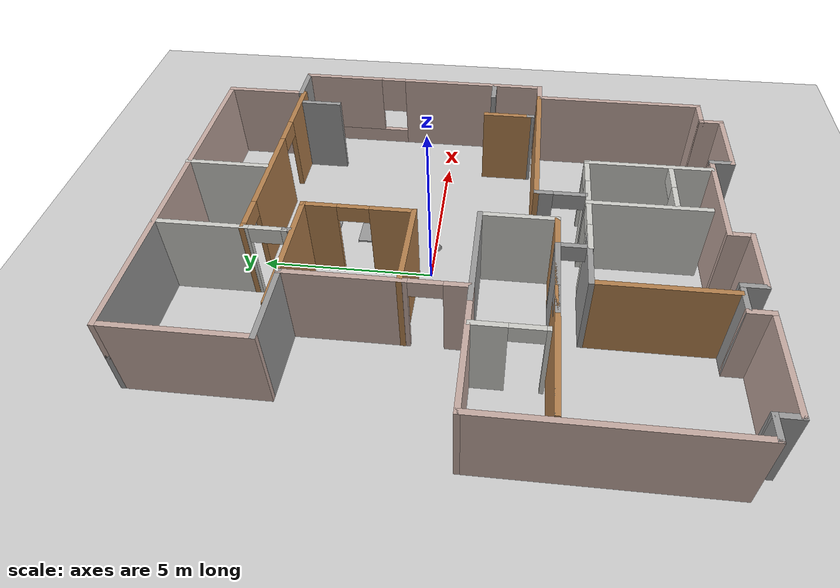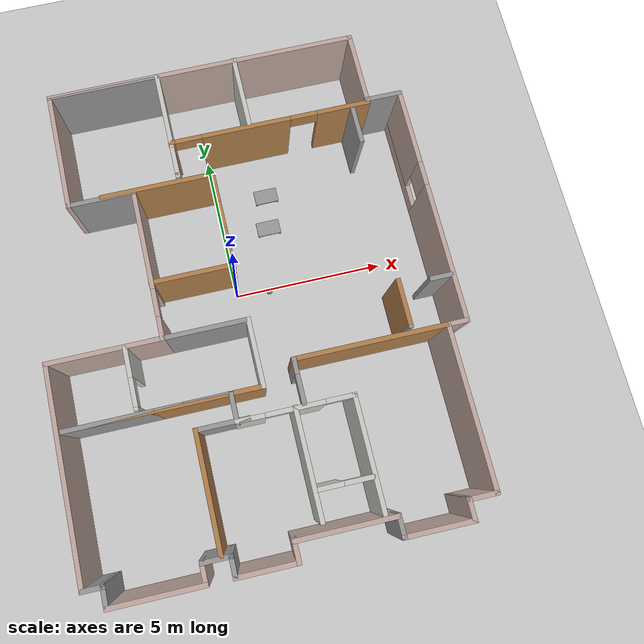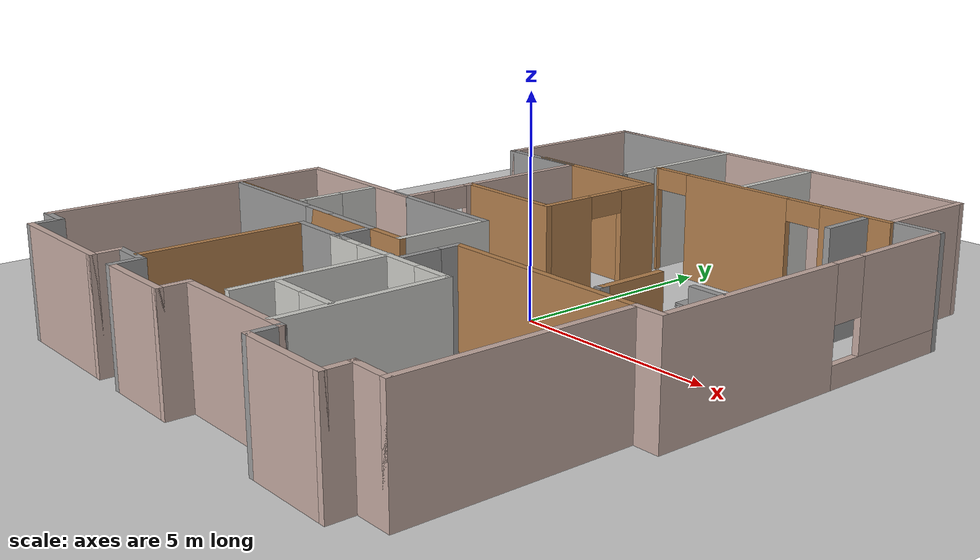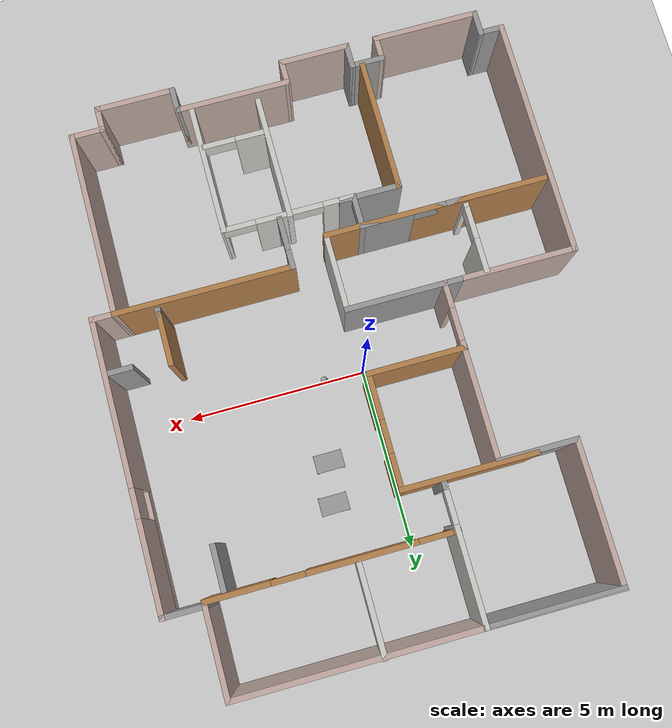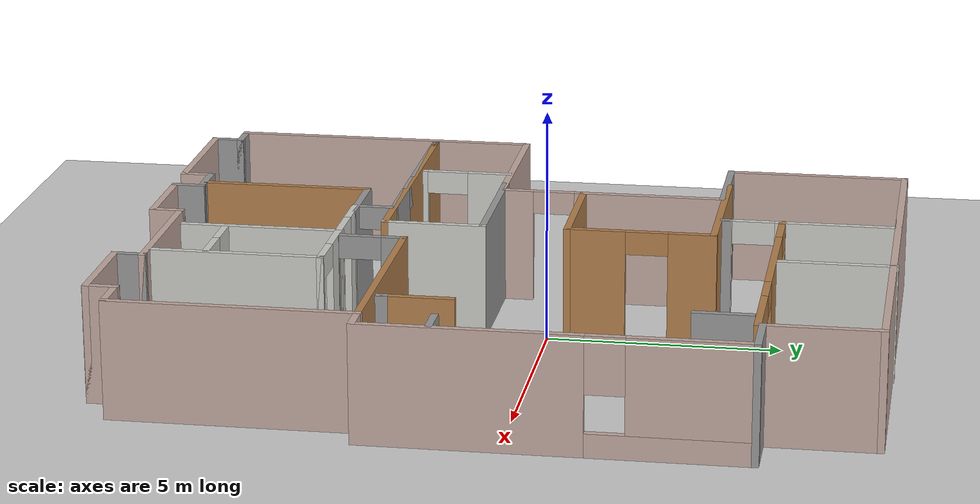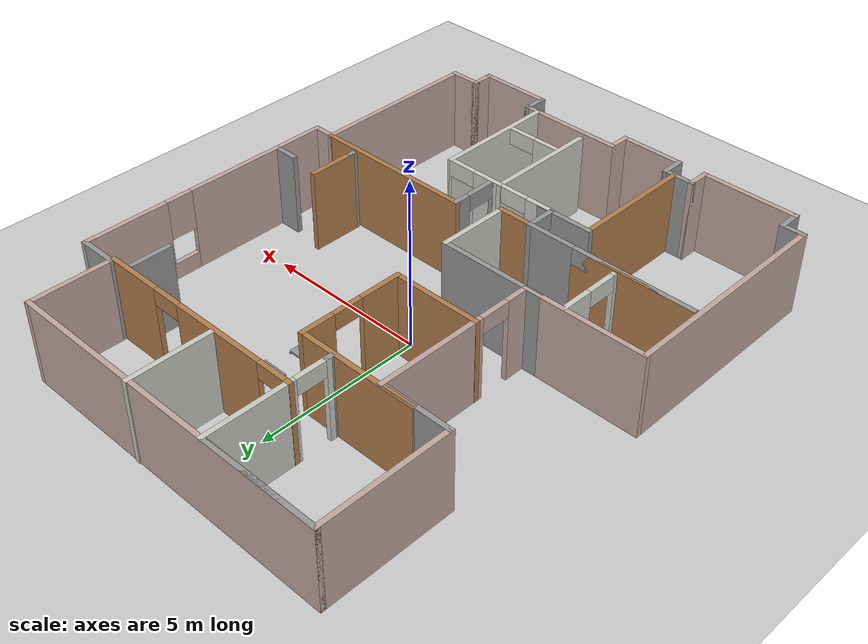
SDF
<sdf version="1.6">
 <world name="default">
  <plugin name="hello_world" filename="../build/libhello_world.so"/>
  <light name="sun" type="directional">
   <pose>0 0 10 0 -0 0</pose>
   <diffuse>0.8 0.8 0.8 1</diffuse>
   <specular>0.2 0.2 0.2 1</specular>
   <attenuation>
    <range>1000</range>
    <constant>0.9</constant>
    <linear>0.01</linear>
    <quadratic>0.001</quadratic>
   </attenuation>
   <direction>-0.5 0.1 -0.9</direction>
  </light>
  <model name="ground_plane">
   <static>1</static>
   <link name="link">
    <collision name="collision">
     <geometry><plane><normal>0 0 1</normal><size>100 100</size></plane></geometry>
     <surface><friction><ode><mu>100</mu><mu2>50</mu2></ode></friction></surface>
    </collision>
    <visual name="visual">
     <cast_shadows>0</cast_shadows>
     <geometry><plane><normal>0 0 1</normal><size>100 100</size></plane></geometry>
     <material>
      <script><uri>file://media/materials/scripts/gazebo.material</uri><name>Gazebo/Grey</name></script>
     </material>
    </visual>
   </link>
  </model>
  <gravity>0 0 -9.8</gravity>
  <magnetic_field>6e-06 2.3e-05 -4.2e-05</magnetic_field>
  <atmosphere type="adiabatic"/>
  <physics name="default_physics" default="0" type="ode">
   <max_step_size>0.001</max_step_size>
   <real_time_factor>1</real_time_factor>
   <real_time_update_rate>1000</real_time_update_rate>
  </physics>
  <scene><ambient>0.4 0.4 0.4 1</ambient><background>0.7 0.7 0.7 1</background><shadows>1</shadows></scene>
  <spherical_coordinates>
   <surface_model>EARTH_WGS84</surface_model>
   <latitude_deg>0</latitude_deg>
   <longitude_deg>0</longitude_deg>
   <elevation>0</elevation>
   <heading_deg>0</heading_deg>
  </spherical_coordinates>
  <model name="wall_v1">
   <pose>0.22839 -0.60462 0 0 -0 0</pose>
   <link name="Wall_1">
    <collision name="Wall_1_Collision">
     <geometry><box><size>4 0.15 2.5</size></box></geometry>
     <pose>0 0 1.25 0 -0 0</pose>
    </collision>
    <visual name="Wall_1_Visual">
     <pose>0 0 1.25 0 -0 0</pose>
     <geometry><box><size>4 0.15 2.5</size></box></geometry>
     <material>
      <script><uri>file://media/materials/scripts/gazebo.material</uri><name>Gazebo/Grey</name></script>
      <ambient>0.760784 0.662745 0.627451 1</ambient>
     </material>
     <meta><layer>0</layer></meta>
    </visual>
    <pose>-4.9 6.0117 0 0 0 -1.5708</pose>
   </link>
   <link name="Wall_10">
    <collision name="Wall_10_Collision">
     <geometry><box><size>1 0.15 2.5</size></box></geometry>
     <pose>0 0 1.25 0 -0 0</pose>
    </collision>
    <visual name="Wall_10_Visual">
     <pose>0 0 1.25 0 -0 0</pose>
     <geometry><box><size>1 0.15 2.5</size></box></geometry>
     <material>
      <script><uri>file://media/materials/scripts/gazebo.material</uri><name>Gazebo/Grey</name></script>
      <ambient>1 1 1 1</ambient>
     </material>
     <meta><layer>0</layer></meta>
    </visual>
    <pose>-2.525 -7.3633 0 0 -0 0</pose>
   </link>
   <link name="Wall_11">
    <collision name="Wall_11_Collision">
     <geometry><box><size>0.75 0.15 2.5</size></box></geometry>
     <pose>0 0 1.25 0 -0 0</pose>
    </collision>
    <visual name="Wall_11_Visual">
     <pose>0 0 1.25 0 -0 0</pose>
     <geometry><box><size>0.75 0.15 2.5</size></box></geometry>
     <material>
      <script><uri>file://media/materials/scripts/gazebo.material</uri><name>Gazebo/Grey</name></script>
      <ambient>1 1 1 1</ambient>
     </material>
     <meta><layer>0</layer></meta>
    </visual>
    <pose>-2.1 -7.6633 0 0 0 -1.5708</pose>
   </link>
   <link name="Wall_12">
    <collision name="Wall_12_Collision">
     <geometry><box><size>2 0.15 2.5</size></box></geometry>
     <pose>0 0 1.25 0 -0 0</pose>
    </collision>
    <visual name="Wall_12_Visual">
     <pose>0 0 1.25 0 -0 0</pose>
     <geometry><box><size>2 0.15 2.5</size></box></geometry>
     <material>
      <script><uri>file://media/materials/scripts/gazebo.material</uri><name>Gazebo/Grey</name></script>
      <ambient>0.760784 0.662745 0.627451 1</ambient>
     </material>
     <meta><layer>0</layer></meta>
    </visual>
    <pose>-1.175 -7.9633 0 0 -0 0</pose>
   </link>
   <link name="Wall_13">
    <collision name="Wall_13_Collision">
     <geometry><box><size>0.75 0.15 2.5</size></box></geometry>
     <pose>0 0 1.25 0 -0 0</pose>
    </collision>
    <visual name="Wall_13_Visual">
     <pose>0 0 1.25 0 -0 0</pose>
     <geometry><box><size>0.75 0.15 2.5</size></box></geometry>
     <material>
      <script><uri>file://media/materials/scripts/gazebo.material</uri><name>Gazebo/Grey</name></script>
      <ambient>0.760784 0.662745 0.627451 1</ambient>
     </material>
     <meta><layer>0</layer></meta>
    </visual>
    <pose>-0.25 -7.6633 0 0 -0 1.5708</pose>
   </link>
   <link name="Wall_14">
    <collision name="Wall_14_Collision">
     <geometry><box><size>3.25 0.15 2.5</size></box></geometry>
     <pose>0 0 1.25 0 -0 0</pose>
    </collision>
    <visual name="Wall_14_Visual">
     <pose>0 0 1.25 0 -0 0</pose>
     <geometry><box><size>3.25 0.15 2.5</size></box></geometry>
     <material>
      <script><uri>file://media/materials/scripts/gazebo.material</uri><name>Gazebo/Grey</name></script>
      <ambient>0.760784 0.662745 0.627451 1</ambient>
     </material>
     <meta><layer>0</layer></meta>
    </visual>
    <pose>1.3 -7.3633 0 0 -0 0</pose>
   </link>
   <link name="Wall_15">
    <collision name="Wall_15_Collision">
     <geometry><box><size>0.75 0.15 2.5</size></box></geometry>
     <pose>0 0 1.25 0 -0 0</pose>
    </collision>
    <visual name="Wall_15_Visual">
     <pose>0 0 1.25 0 -0 0</pose>
     <geometry><box><size>0.75 0.15 2.5</size></box></geometry>
     <material>
      <script><uri>file://media/materials/scripts/gazebo.material</uri><name>Gazebo/Grey</name></script>
      <ambient>1 1 1 1</ambient>
     </material>
     <meta><layer>0</layer></meta>
    </visual>
    <pose>2.85 -7.6633 0 0 0 -1.5708</pose>
   </link>
   <link name="Wall_16">
    <collision name="Wall_16_Collision">
     <geometry><box><size>2.25 0.15 2.5</size></box></geometry>
     <pose>0 0 1.25 0 -0 0</pose>
    </collision>
    <visual name="Wall_16_Visual">
     <pose>0 0 1.25 0 -0 0</pose>
     <geometry><box><size>2.25 0.15 2.5</size></box></geometry>
     <material>
      <script><uri>file://media/materials/scripts/gazebo.material</uri><name>Gazebo/Grey</name></script>
      <ambient>0.760784 0.662745 0.627451 1</ambient>
     </material>
     <meta><layer>0</layer></meta>
    </visual>
    <pose>3.9 -7.9633 0 0 -0 0</pose>
   </link>
   <link name="Wall_17">
    <collision name="Wall_17_Collision">
     <geometry><box><size>0.75 0.15 2.5</size></box></geometry>
     <pose>0 0 1.25 0 -0 0</pose>
    </collision>
    <visual name="Wall_17_Visual">
     <pose>0 0 1.25 0 -0 0</pose>
     <geometry><box><size>0.75 0.15 2.5</size></box></geometry>
     <material>
      <script><uri>file://media/materials/scripts/gazebo.material</uri><name>Gazebo/Grey</name></script>
      <ambient>0.760784 0.662745 0.627451 1</ambient>
     </material>
     <meta><layer>0</layer></meta>
    </visual>
    <pose>4.95 -7.6633 0 0 -0 1.5708</pose>
   </link>
   <link name="Wall_18">
    <collision name="Wall_18_Collision">
     <geometry><box><size>1 0.15 2.5</size></box></geometry>
     <pose>0 0 1.25 0 -0 0</pose>
    </collision>
    <visual name="Wall_18_Visual">
     <pose>0 0 1.25 0 -0 0</pose>
     <geometry><box><size>1 0.15 2.5</size></box></geometry>
     <material>
      <script><uri>file://media/materials/scripts/gazebo.material</uri><name>Gazebo/Grey</name></script>
      <ambient>0.760784 0.662745 0.627451 1</ambient>
     </material>
     <meta><layer>0</layer></meta>
    </visual>
    <pose>5.375 -7.3633 0 0 -0 0</pose>
   </link>
   <link name="Wall_19">
    <collision name="Wall_19_Collision">
     <geometry><box><size>5.25 0.15 2.5</size></box></geometry>
     <pose>0 0 1.25 0 -0 0</pose>
    </collision>
    <visual name="Wall_19_Visual">
     <pose>0 0 1.25 0 -0 0</pose>
     <geometry><box><size>5.25 0.15 2.5</size></box></geometry>
     <material>
      <script><uri>file://media/materials/scripts/gazebo.material</uri><name>Gazebo/Grey</name></script>
      <ambient>0.760784 0.662745 0.627451 1</ambient>
     </material>
     <meta><layer>0</layer></meta>
    </visual>
    <pose>5.8 -4.8133 0 0 -0 1.5708</pose>
   </link>
   <link name="Wall_2">
    <collision name="Wall_2_Collision">
     <geometry><box><size>2.25 0.15 2.5</size></box></geometry>
     <pose>0 0 1.25 0 -0 0</pose>
    </collision>
    <visual name="Wall_2_Visual">
     <pose>0 0 1.25 0 -0 0</pose>
     <geometry><box><size>2.25 0.15 2.5</size></box></geometry>
     <material>
      <script><uri>file://media/materials/scripts/gazebo.material</uri><name>Gazebo/Grey</name></script>
      <ambient>1 1 1 1</ambient>
     </material>
     <meta><layer>0</layer></meta>
    </visual>
    <pose>-3.85 4.0867 0 0 -0 0</pose>
   </link>
   <link name="Wall_20">
    <collision name="Wall_20_Collision">
     <geometry><box><size>0.75 0.15 2.5</size></box></geometry>
     <pose>0 0 1.25 0 -0 0</pose>
    </collision>
    <visual name="Wall_20_Visual">
     <pose>0 0 1.25 0 -0 0</pose>
     <geometry><box><size>0.75 0.15 2.5</size></box></geometry>
     <material>
      <script><uri>file://media/materials/scripts/gazebo.material</uri><name>Gazebo/Grey</name></script>
      <ambient>0.760784 0.662745 0.627451 1</ambient>
     </material>
     <meta><layer>0</layer></meta>
    </visual>
    <pose>6.1 -2.2633 0 0 -0 0</pose>
   </link>
   <link name="Wall_21">
    <pose>6.4 1.6617 0 0 -0 1.5708</pose>
    <visual name="Wall_21_Visual_0">
     <pose>-1.69592 0 1.25 0 -0 0</pose>
     <geometry><box><size>4.60816 0.15 2.5</size></box></geometry>
     <material>
      <script><uri>file://media/materials/scripts/gazebo.material</uri><name>Gazebo/Grey</name></script>
      <ambient>0.760784 0.662745 0.627451 1</ambient>
     </material>
     <meta><layer>0</layer></meta>
    </visual>
    <collision name="Wall_21_Collision_0">
     <geometry><box><size>4.60816 0.15 2.5</size></box></geometry>
     <pose>-1.69592 0 1.25 0 -0 0</pose>
    </collision>
    <visual name="Wall_21_Visual_1">
     <pose>2.30408 0 0.25 0 -0 0</pose>
     <geometry><box><size>3.39184 0.15 0.5</size></box></geometry>
     <material>
      <script><uri>file://media/materials/scripts/gazebo.material</uri><name>Gazebo/Grey</name></script>
      <ambient>0.760784 0.662745 0.627451 1</ambient>
     </material>
     <meta><layer>0</layer></meta>
    </visual>
    <collision name="Wall_21_Collision_1">
     <geometry><box><size>3.39184 0.15 0.5</size></box></geometry>
     <pose>2.30408 0 0.25 0 -0 0</pose>
    </collision>
    <visual name="Wall_21_Visual_2">
     <pose>2.70408 0 1.5 0 -0 0</pose>
     <geometry><box><size>2.59184 0.15 2</size></box></geometry>
     <material>
      <script><uri>file://media/materials/scripts/gazebo.material</uri><name>Gazebo/Grey</name></script>
      <ambient>0.760784 0.662745 0.627451 1</ambient>
     </material>
     <meta><layer>0</layer></meta>
    </visual>
    <collision name="Wall_21_Collision_2">
     <geometry><box><size>2.59184 0.15 2</size></box></geometry>
     <pose>2.70408 0 1.5 0 -0 0</pose>
    </collision>
    <visual name="Wall_21_Visual_3">
     <pose>1.00816 0 1.9 0 -0 0</pose>
     <geometry><box><size>0.8 0.15 1.2</size></box></geometry>
     <material>
      <script><uri>file://media/materials/scripts/gazebo.material</uri><name>Gazebo/Grey</name></script>
      <ambient>0.760784 0.662745 0.627451 1</ambient>
     </material>
     <meta><layer>0</layer></meta>
    </visual>
    <collision name="Wall_21_Collision_3">
     <geometry><box><size>0.8 0.15 1.2</size></box></geometry>
     <pose>1.00816 0 1.9 0 -0 0</pose>
    </collision>
   </link>
   <link name="Wall_22">
    <collision name="Wall_22_Collision">
     <geometry><box><size>1.25 0.15 2.5</size></box></geometry>
     <pose>0 0 1.25 0 -0 0</pose>
    </collision>
    <visual name="Wall_22_Visual">
     <pose>0 0 1.25 0 -0 0</pose>
     <geometry><box><size>1.25 0.15 2.5</size></box></geometry>
     <material>
      <script><uri>file://media/materials/scripts/gazebo.material</uri><name>Gazebo/Grey</name></script>
      <ambient>1 1 1 1</ambient>
     </material>
     <meta><layer>0</layer></meta>
    </visual>
    <pose>5.85 5.5867 0 0 -0 3.14159</pose>
   </link>
   <link name="Wall_23">
    <collision name="Wall_23_Collision">
     <geometry><box><size>2.5 0.15 2.5</size></box></geometry>
     <pose>0 0 1.25 0 -0 0</pose>
    </collision>
    <visual name="Wall_23_Visual">
     <pose>0 0 1.25 0 -0 0</pose>
     <geometry><box><size>2.5 0.15 2.5</size></box></geometry>
     <material>
      <script><uri>file://media/materials/scripts/gazebo.material</uri><name>Gazebo/Grey</name></script>
      <ambient>0.760784 0.662745 0.627451 1</ambient>
     </material>
     <meta><layer>0</layer></meta>
    </visual>
    <pose>5.3 6.7617 0 0 -0 1.5708</pose>
   </link>
   <link name="Wall_24">
    <collision name="Wall_24_Collision">
     <geometry><box><size>10.35 0.15 2.5</size></box></geometry>
     <pose>0 0 1.25 0 -0 0</pose>
    </collision>
    <visual name="Wall_24_Visual">
     <pose>0 0 1.25 0 -0 0</pose>
     <geometry><box><size>10.35 0.15 2.5</size></box></geometry>
     <material>
      <script><uri>file://media/materials/scripts/gazebo.material</uri><name>Gazebo/Grey</name></script>
      <ambient>0.760784 0.662745 0.627451 1</ambient>
     </material>
     <meta><layer>0</layer></meta>
    </visual>
    <pose>0.2 7.9367 0 0 -0 3.14159</pose>
   </link>
   <link name="Wall_25">
    <collision name="Wall_25_Collision">
     <geometry><box><size>3.75 0.15 2.5</size></box></geometry>
     <pose>0 0 1.25 0 -0 0</pose>
    </collision>
    <visual name="Wall_25_Visual">
     <pose>0 0 1.25 0 -0 0</pose>
     <geometry><box><size>3.75 0.15 2.5</size></box></geometry>
     <material>
      <script><uri>file://media/materials/scripts/gazebo.material</uri><name>Gazebo/Grey</name></script>
      <ambient>1 1 1 1</ambient>
     </material>
     <meta><layer>0</layer></meta>
    </visual>
    <pose>-3.1 7.9367 0 0 -0 0</pose>
   </link>
   <link name="Wall_26">
    <pose>-1.3 6.1367 0 0 0 -1.5708</pose>
    <visual name="Wall_26_Visual_0">
     <pose>-0.532989 0 1.25 0 -0 0</pose>
     <geometry><box><size>2.68402 0.15 2.5</size></box></geometry>
     <material>
      <script><uri>file://media/materials/scripts/gazebo.material</uri><name>Gazebo/CeilingTiled</name></script>
      <ambient>1 1 1 1</ambient>
     </material>
     <meta><layer>0</layer></meta>
    </visual>
    <collision name="Wall_26_Collision_0">
     <geometry><box><size>2.68402 0.15 2.5</size></box></geometry>
     <pose>-0.532989 0 1.25 0 -0 0</pose>
    </collision>
    <visual name="Wall_26_Visual_1">
     <pose>1.79201 0 1.25 0 -0 0</pose>
     <geometry><box><size>0.165977 0.15 2.5</size></box></geometry>
     <material>
      <script><uri>file://media/materials/scripts/gazebo.material</uri><name>Gazebo/CeilingTiled</name></script>
      <ambient>1 1 1 1</ambient>
     </material>
     <meta><layer>0</layer></meta>
    </visual>
    <collision name="Wall_26_Collision_1">
     <geometry><box><size>0.165977 0.15 2.5</size></box></geometry>
     <pose>1.79201 0 1.25 0 -0 0</pose>
    </collision>
    <visual name="Wall_26_Visual_2">
     <pose>1.25902 0 2.25 0 -0 0</pose>
     <geometry><box><size>0.9 0.15 0.5</size></box></geometry>
     <material>
      <script><uri>file://media/materials/scripts/gazebo.material</uri><name>Gazebo/CeilingTiled</name></script>
      <ambient>1 1 1 1</ambient>
     </material>
     <meta><layer>0</layer></meta>
    </visual>
    <collision name="Wall_26_Collision_2">
     <geometry><box><size>0.9 0.15 0.5</size></box></geometry>
     <pose>1.25902 0 2.25 0 -0 0</pose>
    </collision>
   </link>
   <link name="Wall_27">
    <collision name="Wall_27_Collision">
     <geometry><box><size>0.25 0.15 2.5</size></box></geometry>
     <pose>0 0 1.25 0 -0 0</pose>
    </collision>
    <visual name="Wall_27_Visual">
     <pose>0 0 1.25 0 -0 0</pose>
     <geometry><box><size>0.25 0.15 2.5</size></box></geometry>
     <material>
      <script><uri>file://media/materials/scripts/gazebo.material</uri><name>Gazebo/Grey</name></script>
      <ambient>1 1 1 1</ambient>
     </material>
     <meta><layer>0</layer></meta>
    </visual>
    <pose>-1.3 4.2867 0 0 0 -1.5708</pose>
   </link>
   <link name="Wall_3">
    <pose>-2.8 1.6617 0 0 0 -1.5708</pose>
    <visual name="Wall_3_Visual_0">
     <pose>-0.835272 0 1.25 0 -0 0</pose>
     <geometry><box><size>3.32946 0.15 2.5</size></box></geometry>
     <material>
      <script><uri>file://media/materials/scripts/gazebo.material</uri><name>Gazebo/Grey</name></script>
      <ambient>0.760784 0.662745 0.627451 1</ambient>
     </material>
     <meta><layer>0</layer></meta>
    </visual>
    <collision name="Wall_3_Collision_0">
     <geometry><box><size>3.32946 0.15 2.5</size></box></geometry>
     <pose>-0.835272 0 1.25 0 -0 0</pose>
    </collision>
    <visual name="Wall_3_Visual_1">
     <pose>2.11473 0 1.25 0 -0 0</pose>
     <geometry><box><size>0.770544 0.15 2.5</size></box></geometry>
     <material>
      <script><uri>file://media/materials/scripts/gazebo.material</uri><name>Gazebo/Grey</name></script>
      <ambient>0.760784 0.662745 0.627451 1</ambient>
     </material>
     <meta><layer>0</layer></meta>
    </visual>
    <collision name="Wall_3_Collision_1">
     <geometry><box><size>0.770544 0.15 2.5</size></box></geometry>
     <pose>2.11473 0 1.25 0 -0 0</pose>
    </collision>
    <visual name="Wall_3_Visual_2">
     <pose>1.27946 0 2.25 0 -0 0</pose>
     <geometry><box><size>0.9 0.15 0.5</size></box></geometry>
     <material>
      <script><uri>file://media/materials/scripts/gazebo.material</uri><name>Gazebo/Grey</name></script>
      <ambient>0.760784 0.662745 0.627451 1</ambient>
     </material>
     <meta><layer>0</layer></meta>
    </visual>
    <collision name="Wall_3_Collision_2">
     <geometry><box><size>0.9 0.15 0.5</size></box></geometry>
     <pose>1.27946 0 2.25 0 -0 0</pose>
    </collision>
   </link>
   <link name="Wall_30">
    <collision name="Wall_30_Collision">
     <geometry><box><size>3.75 0.15 2.5</size></box></geometry>
     <pose>0 0 1.25 0 -0 0</pose>
    </collision>
    <visual name="Wall_30_Visual">
     <pose>0 0 1.25 0 -0 0</pose>
     <geometry><box><size>3.75 0.15 2.5</size></box></geometry>
     <material>
      <script><uri>file://media/materials/scripts/gazebo.material</uri><name>Gazebo/Wood</name></script>
      <ambient>1 1 1 1</ambient>
     </material>
     <meta><layer>0</layer></meta>
    </visual>
    <pose>-2.00939 4.13287 0 0 -0 0</pose>
   </link>
   <link name="Wall_31">
    <pose>-0.209392 2.58287 0 0 0 -1.5708</pose>
    <visual name="Wall_31_Visual_0">
     <pose>-1.1076 0 1.25 0 -0 0</pose>
     <geometry><box><size>1.03481 0.15 2.5</size></box></geometry>
     <material>
      <script><uri>file://media/materials/scripts/gazebo.material</uri><name>Gazebo/Wood</name></script>
      <ambient>1 1 1 1</ambient>
     </material>
     <meta><layer>0</layer></meta>
    </visual>
    <collision name="Wall_31_Collision_0">
     <geometry><box><size>1.03481 0.15 2.5</size></box></geometry>
     <pose>-1.1076 0 1.25 0 -0 0</pose>
    </collision>
    <visual name="Wall_31_Visual_1">
     <pose>0.967405 0 1.25 0 -0 0</pose>
     <geometry><box><size>1.31519 0.15 2.5</size></box></geometry>
     <material>
      <script><uri>file://media/materials/scripts/gazebo.material</uri><name>Gazebo/Wood</name></script>
      <ambient>1 1 1 1</ambient>
     </material>
     <meta><layer>0</layer></meta>
    </visual>
    <collision name="Wall_31_Collision_1">
     <geometry><box><size>1.31519 0.15 2.5</size></box></geometry>
     <pose>0.967405 0 1.25 0 -0 0</pose>
    </collision>
    <visual name="Wall_31_Visual_2">
     <pose>-0.140189 0 2.25 0 -0 0</pose>
     <geometry><box><size>0.9 0.15 0.5</size></box></geometry>
     <material>
      <script><uri>file://media/materials/scripts/gazebo.material</uri><name>Gazebo/Wood</name></script>
      <ambient>1 1 1 1</ambient>
     </material>
     <meta><layer>0</layer></meta>
    </visual>
    <collision name="Wall_31_Collision_2">
     <geometry><box><size>0.9 0.15 0.5</size></box></geometry>
     <pose>-0.140189 0 2.25 0 -0 0</pose>
    </collision>
   </link>
   <link name="Wall_32">
    <collision name="Wall_32_Collision">
     <geometry><box><size>2.75 0.15 2.5</size></box></geometry>
     <pose>0 0 1.25 0 -0 0</pose>
    </collision>
    <visual name="Wall_32_Visual">
     <pose>0 0 1.25 0 -0 0</pose>
     <geometry><box><size>2.75 0.15 2.5</size></box></geometry>
     <material>
      <script><uri>file://media/materials/scripts/gazebo.material</uri><name>Gazebo/Wood</name></script>
      <ambient>1 1 1 1</ambient>
     </material>
     <meta><layer>0</layer></meta>
    </visual>
    <pose>-1.50939 1.03287 0 0 -0 3.14159</pose>
   </link>
   <link name="Wall_34">
    <collision name="Wall_34_Collision">
     <geometry><box><size>3.25 0.15 2.5</size></box></geometry>
     <pose>0 0 1.25 0 -0 0</pose>
    </collision>
    <visual name="Wall_34_Visual">
     <pose>0 0 1.25 0 -0 0</pose>
     <geometry><box><size>3.25 0.15 2.5</size></box></geometry>
     <material>
      <script><uri>file://media/materials/scripts/gazebo.material</uri><name>Gazebo/Grey</name></script>
      <ambient>1 1 1 1</ambient>
     </material>
     <meta><layer>0</layer></meta>
    </visual>
    <pose>-1.67419 -0.761565 0 0 -0 0</pose>
   </link>
   <link name="Wall_35">
    <collision name="Wall_35_Collision">
     <geometry><box><size>2.25 0.15 2.5</size></box></geometry>
     <pose>0 0 1.25 0 -0 0</pose>
    </collision>
    <visual name="Wall_35_Visual">
     <pose>0 0 1.25 0 -0 0</pose>
     <geometry><box><size>2.25 0.15 2.5</size></box></geometry>
     <material>
      <script><uri>file://media/materials/scripts/gazebo.material</uri><name>Gazebo/CeilingTiled</name></script>
      <ambient>1 1 1 1</ambient>
     </material>
     <meta><layer>0</layer></meta>
    </visual>
    <pose>-0.124188 -1.81157 0 0 0 -1.5708</pose>
   </link>
   <link name="Wall_36">
    <collision name="Wall_36_Collision">
     <geometry><box><size>6.25 0.15 2.5</size></box></geometry>
     <pose>0 0 1.25 0 -0 0</pose>
    </collision>
    <visual name="Wall_36_Visual">
     <pose>0 0 1.25 0 -0 0</pose>
     <geometry><box><size>6.25 0.15 2.5</size></box></geometry>
     <material>
      <script><uri>file://media/materials/scripts/gazebo.material</uri><name>Gazebo/Wood</name></script>
      <ambient>1 1 1 1</ambient>
     </material>
     <meta><layer>0</layer></meta>
    </visual>
    <pose>-3.17419 -2.86157 0 0 -0 3.14159</pose>
   </link>
   <link name="Wall_37">
    <pose>-3.67419 -2.86157 0 0 -0 0</pose>
    <visual name="Wall_37_Visual_0">
     <pose>-1.2061 0 1.25 0 -0 0</pose>
     <geometry><box><size>2.8378 0.15 2.5</size></box></geometry>
     <material>
      <script><uri>file://media/materials/scripts/gazebo.material</uri><name>Gazebo/Grey</name></script>
      <ambient>1 1 1 1</ambient>
     </material>
     <meta><layer>0</layer></meta>
    </visual>
    <collision name="Wall_37_Collision_0">
     <geometry><box><size>2.8378 0.15 2.5</size></box></geometry>
     <pose>-1.2061 0 1.25 0 -0 0</pose>
    </collision>
    <visual name="Wall_37_Visual_1">
     <pose>1.8689 0 1.25 0 -0 0</pose>
     <geometry><box><size>1.5122 0.15 2.5</size></box></geometry>
     <material>
      <script><uri>file://media/materials/scripts/gazebo.material</uri><name>Gazebo/Grey</name></script>
      <ambient>1 1 1 1</ambient>
     </material>
     <meta><layer>0</layer></meta>
    </visual>
    <collision name="Wall_37_Collision_1">
     <geometry><box><size>1.5122 0.15 2.5</size></box></geometry>
     <pose>1.8689 0 1.25 0 -0 0</pose>
    </collision>
    <visual name="Wall_37_Visual_2">
     <pose>0.662802 0 2.25 0 -0 0</pose>
     <geometry><box><size>0.9 0.15 0.5</size></box></geometry>
     <material>
      <script><uri>file://media/materials/scripts/gazebo.material</uri><name>Gazebo/Grey</name></script>
      <ambient>1 1 1 1</ambient>
     </material>
     <meta><layer>0</layer></meta>
    </visual>
    <collision name="Wall_37_Collision_2">
     <geometry><box><size>0.9 0.15 0.5</size></box></geometry>
     <pose>0.662802 0 2.25 0 -0 0</pose>
    </collision>
   </link>
   <link name="Wall_38">
    <pose>-1.12419 -3.28656 0 0 0 -1.5708</pose>
    <visual name="Wall_38_Visual_0">
     <pose>-0.487291 0 1.25 0 -0 0</pose>
     <geometry><box><size>0.025419 0.15 2.5</size></box></geometry>
     <material>
      <script><uri>file://media/materials/scripts/gazebo.material</uri><name>Gazebo/Grey</name></script>
      <ambient>1 1 1 1</ambient>
     </material>
     <meta><layer>0</layer></meta>
    </visual>
    <collision name="Wall_38_Collision_0">
     <geometry><box><size>0.025419 0.15 2.5</size></box></geometry>
     <pose>-0.487291 0 1.25 0 -0 0</pose>
    </collision>
    <visual name="Wall_38_Visual_1">
     <pose>0.462709 0 1.25 0 -0 0</pose>
     <geometry><box><size>0.074581 0.15 2.5</size></box></geometry>
     <material>
      <script><uri>file://media/materials/scripts/gazebo.material</uri><name>Gazebo/Grey</name></script>
      <ambient>1 1 1 1</ambient>
     </material>
     <meta><layer>0</layer></meta>
    </visual>
    <collision name="Wall_38_Collision_1">
     <geometry><box><size>0.074581 0.15 2.5</size></box></geometry>
     <pose>0.462709 0 1.25 0 -0 0</pose>
    </collision>
    <visual name="Wall_38_Visual_2">
     <pose>-0.024581 0 2.25 0 -0 0</pose>
     <geometry><box><size>0.9 0.15 0.5</size></box></geometry>
     <material>
      <script><uri>file://media/materials/scripts/gazebo.material</uri><name>Gazebo/Grey</name></script>
      <ambient>1 1 1 1</ambient>
     </material>
     <meta><layer>0</layer></meta>
    </visual>
    <collision name="Wall_38_Collision_2">
     <geometry><box><size>0.9 0.15 0.5</size></box></geometry>
     <pose>-0.024581 0 2.25 0 -0 0</pose>
    </collision>
   </link>
   <link name="Wall_39">
    <pose>0.675812 -3.71156 0 0 -0 0</pose>
    <visual name="Wall_39_Visual_0">
     <pose>-1.41009 0 1.25 0 -0 0</pose>
     <geometry><box><size>0.929825 0.15 2.5</size></box></geometry>
     <material>
      <script><uri>file://media/materials/scripts/gazebo.material</uri><name>Gazebo/CeilingTiled</name></script>
      <ambient>1 1 1 1</ambient>
     </material>
     <meta><layer>0</layer></meta>
    </visual>
    <collision name="Wall_39_Collision_0">
     <geometry><box><size>0.929825 0.15 2.5</size></box></geometry>
     <pose>-1.41009 0 1.25 0 -0 0</pose>
    </collision>
    <visual name="Wall_39_Visual_1">
     <pose>0.435832 0 1.25 0 -0 0</pose>
     <geometry><box><size>0.962014 0.15 2.5</size></box></geometry>
     <material>
      <script><uri>file://media/materials/scripts/gazebo.material</uri><name>Gazebo/CeilingTiled</name></script>
      <ambient>1 1 1 1</ambient>
     </material>
     <meta><layer>0</layer></meta>
    </visual>
    <collision name="Wall_39_Collision_1">
     <geometry><box><size>0.962014 0.15 2.5</size></box></geometry>
     <pose>0.435832 0 1.25 0 -0 0</pose>
    </collision>
    <visual name="Wall_39_Visual_2">
     <pose>1.84592 0 1.25 0 -0 0</pose>
     <geometry><box><size>0.058161 0.15 2.5</size></box></geometry>
     <material>
      <script><uri>file://media/materials/scripts/gazebo.material</uri><name>Gazebo/CeilingTiled</name></script>
      <ambient>1 1 1 1</ambient>
     </material>
     <meta><layer>0</layer></meta>
    </visual>
    <collision name="Wall_39_Collision_2">
     <geometry><box><size>0.058161 0.15 2.5</size></box></geometry>
     <pose>1.84592 0 1.25 0 -0 0</pose>
    </collision>
    <visual name="Wall_39_Visual_3">
     <pose>-0.495175 0 2.25 0 -0 0</pose>
     <geometry><box><size>0.9 0.15 0.5</size></box></geometry>
     <material>
      <script><uri>file://media/materials/scripts/gazebo.material</uri><name>Gazebo/CeilingTiled</name></script>
      <ambient>1 1 1 1</ambient>
     </material>
     <meta><layer>0</layer></meta>
    </visual>
    <collision name="Wall_39_Collision_3">
     <geometry><box><size>0.9 0.15 0.5</size></box></geometry>
     <pose>-0.495175 0 2.25 0 -0 0</pose>
    </collision>
    <visual name="Wall_39_Visual_4">
     <pose>1.36684 0 2.25 0 -0 0</pose>
     <geometry><box><size>0.9 0.15 0.5</size></box></geometry>
     <material>
      <script><uri>file://media/materials/scripts/gazebo.material</uri><name>Gazebo/CeilingTiled</name></script>
      <ambient>1 1 1 1</ambient>
     </material>
     <meta><layer>0</layer></meta>
    </visual>
    <collision name="Wall_39_Collision_4">
     <geometry><box><size>0.9 0.15 0.5</size></box></geometry>
     <pose>1.36684 0 2.25 0 -0 0</pose>
    </collision>
   </link>
   <link name="Wall_4">
    <collision name="Wall_4_Collision">
     <geometry><box><size>3.75 0.15 2.5</size></box></geometry>
     <pose>0 0 1.25 0 -0 0</pose>
    </collision>
    <visual name="Wall_4_Visual">
     <pose>0 0 1.25 0 -0 0</pose>
     <geometry><box><size>3.75 0.15 2.5</size></box></geometry>
     <material>
      <script><uri>file://media/materials/scripts/gazebo.material</uri><name>Gazebo/Grey</name></script>
      <ambient>0.760784 0.662745 0.627451 1</ambient>
     </material>
     <meta><layer>0</layer></meta>
    </visual>
    <pose>-4.6 -0.7633 0 0 -0 3.14159</pose>
   </link>
   <link name="Wall_40">
    <collision name="Wall_40_Collision">
     <geometry><box><size>3.75 0.15 2.5</size></box></geometry>
     <pose>0 0 1.25 0 -0 0</pose>
    </collision>
    <visual name="Wall_40_Visual">
     <pose>0 0 1.25 0 -0 0</pose>
     <geometry><box><size>3.75 0.15 2.5</size></box></geometry>
     <material>
      <script><uri>file://media/materials/scripts/gazebo.material</uri><name>Gazebo/CeilingTiled</name></script>
      <ambient>1 1 1 1</ambient>
     </material>
     <meta><layer>0</layer></meta>
    </visual>
    <pose>2.47581 -5.51157 0 0 0 -1.5708</pose>
   </link>
   <link name="Wall_42">
    <collision name="Wall_42_Collision">
     <geometry><box><size>3.5 0.15 2.5</size></box></geometry>
     <pose>0 0 1.25 0 -0 0</pose>
    </collision>
    <visual name="Wall_42_Visual">
     <pose>0 0 1.25 0 -0 0</pose>
     <geometry><box><size>3.5 0.15 2.5</size></box></geometry>
     <material>
      <script><uri>file://media/materials/scripts/gazebo.material</uri><name>Gazebo/CeilingTiled</name></script>
      <ambient>1 1 1 1</ambient>
     </material>
     <meta><layer>0</layer></meta>
    </visual>
    <pose>0.659442 -5.36259 0 0 0 -1.5708</pose>
   </link>
   <link name="Wall_44">
    <collision name="Wall_44_Collision">
     <geometry><box><size>1.75 0.15 2.5</size></box></geometry>
     <pose>0 0 1.25 0 -0 0</pose>
    </collision>
    <visual name="Wall_44_Visual">
     <pose>0 0 1.25 0 -0 0</pose>
     <geometry><box><size>1.75 0.15 2.5</size></box></geometry>
     <material>
      <script><uri>file://media/materials/scripts/gazebo.material</uri><name>Gazebo/Grey</name></script>
      <ambient>1 1 1 1</ambient>
     </material>
     <meta><layer>0</layer></meta>
    </visual>
    <pose>-1.57697 -3.68759 0 0 -0 3.14159</pose>
   </link>
   <link name="Wall_45">
    <collision name="Wall_45_Collision">
     <geometry><box><size>3.75 0.15 2.5</size></box></geometry>
     <pose>0 0 1.25 0 -0 0</pose>
    </collision>
    <visual name="Wall_45_Visual">
     <pose>0 0 1.25 0 -0 0</pose>
     <geometry><box><size>3.75 0.15 2.5</size></box></geometry>
     <material>
      <script><uri>file://media/materials/scripts/gazebo.material</uri><name>Gazebo/Wood</name></script>
      <ambient>1 1 1 1</ambient>
     </material>
     <meta><layer>0</layer></meta>
    </visual>
    <pose>-2.37697 -5.48759 0 0 0 -1.5708</pose>
   </link>
   <link name="Wall_47">
    <pose>-3.96899 -1.73977 0 0 0 -1.5708</pose>
    <visual name="Wall_47_Visual_0">
     <pose>-0.509195 0 1.25 0 -0 0</pose>
     <geometry><box><size>0.98161 0.15 2.5</size></box></geometry>
     <material>
      <script><uri>file://media/materials/scripts/gazebo.material</uri><name>Gazebo/CeilingTiled</name></script>
      <ambient>1 1 1 1</ambient>
     </material>
     <meta><layer>0</layer></meta>
    </visual>
    <collision name="Wall_47_Collision_0">
     <geometry><box><size>0.98161 0.15 2.5</size></box></geometry>
     <pose>-0.509195 0 1.25 0 -0 0</pose>
    </collision>
    <visual name="Wall_47_Visual_1">
     <pose>0.940805 0 1.25 0 -0 0</pose>
     <geometry><box><size>0.11839 0.15 2.5</size></box></geometry>
     <material>
      <script><uri>file://media/materials/scripts/gazebo.material</uri><name>Gazebo/CeilingTiled</name></script>
      <ambient>1 1 1 1</ambient>
     </material>
     <meta><layer>0</layer></meta>
    </visual>
    <collision name="Wall_47_Collision_1">
     <geometry><box><size>0.11839 0.15 2.5</size></box></geometry>
     <pose>0.940805 0 1.25 0 -0 0</pose>
    </collision>
    <visual name="Wall_47_Visual_2">
     <pose>0.43161 0 2.25 0 -0 0</pose>
     <geometry><box><size>0.9 0.15 0.5</size></box></geometry>
     <material>
      <script><uri>file://media/materials/scripts/gazebo.material</uri><name>Gazebo/CeilingTiled</name></script>
      <ambient>1 1 1 1</ambient>
     </material>
     <meta><layer>0</layer></meta>
    </visual>
    <collision name="Wall_47_Collision_2">
     <geometry><box><size>0.9 0.15 0.5</size></box></geometry>
     <pose>0.43161 0 2.25 0 -0 0</pose>
    </collision>
   </link>
   <link name="Wall_49">
    <pose>1.59244 -6.13481 0 0 -0 0</pose>
    <visual name="Wall_49_Visual_0">
     <pose>-0.463996 0 1.25 0 -0 0</pose>
     <geometry><box><size>0.822009 0.15 2.5</size></box></geometry>
     <material>
      <script><uri>file://media/materials/scripts/gazebo.material</uri><name>Gazebo/CeilingTiled</name></script>
      <ambient>1 1 1 1</ambient>
     </material>
     <meta><layer>0</layer></meta>
    </visual>
    <collision name="Wall_49_Collision_0">
     <geometry><box><size>0.822009 0.15 2.5</size></box></geometry>
     <pose>-0.463996 0 1.25 0 -0 0</pose>
    </collision>
    <visual name="Wall_49_Visual_1">
     <pose>0.861004 0 1.25 0 -0 0</pose>
     <geometry><box><size>0.027991 0.15 2.5</size></box></geometry>
     <material>
      <script><uri>file://media/materials/scripts/gazebo.material</uri><name>Gazebo/CeilingTiled</name></script>
      <ambient>1 1 1 1</ambient>
     </material>
     <meta><layer>0</layer></meta>
    </visual>
    <collision name="Wall_49_Collision_1">
     <geometry><box><size>0.027991 0.15 2.5</size></box></geometry>
     <pose>0.861004 0 1.25 0 -0 0</pose>
    </collision>
    <visual name="Wall_49_Visual_2">
     <pose>0.397009 0 2.25 0 -0 0</pose>
     <geometry><box><size>0.9 0.15 0.5</size></box></geometry>
     <material>
      <script><uri>file://media/materials/scripts/gazebo.material</uri><name>Gazebo/CeilingTiled</name></script>
      <ambient>1 1 1 1</ambient>
     </material>
     <meta><layer>0</layer></meta>
    </visual>
    <collision name="Wall_49_Collision_2">
     <geometry><box><size>0.9 0.15 0.5</size></box></geometry>
     <pose>0.397009 0 2.25 0 -0 0</pose>
    </collision>
   </link>
   <link name="Wall_5">
    <collision name="Wall_5_Collision">
     <geometry><box><size>6.75 0.15 2.5</size></box></geometry>
     <pose>0 0 1.25 0 -0 0</pose>
    </collision>
    <visual name="Wall_5_Visual">
     <pose>0 0 1.25 0 -0 0</pose>
     <geometry><box><size>6.75 0.15 2.5</size></box></geometry>
     <material>
      <script><uri>file://media/materials/scripts/gazebo.material</uri><name>Gazebo/Grey</name></script>
      <ambient>0.760784 0.662745 0.627451 1</ambient>
     </material>
     <meta><layer>0</layer></meta>
    </visual>
    <pose>-6.4 -4.0633 0 0 0 -1.5708</pose>
   </link>
   <link name="Wall_51">
    <pose>1.99103 5.48948 0 0 -0 0</pose>
    <visual name="Wall_51_Visual_0">
     <pose>-3.2699 0 1.25 0 -0 0</pose>
     <geometry><box><size>0.210204 0.15 2.5</size></box></geometry>
     <material>
      <script><uri>file://media/materials/scripts/gazebo.material</uri><name>Gazebo/Wood</name></script>
      <ambient>1 1 1 1</ambient>
     </material>
     <meta><layer>0</layer></meta>
    </visual>
    <collision name="Wall_51_Collision_0">
     <geometry><box><size>0.210204 0.15 2.5</size></box></geometry>
     <pose>-3.2699 0 1.25 0 -0 0</pose>
    </collision>
    <visual name="Wall_51_Visual_1">
     <pose>-0.786281 0 1.25 0 -0 0</pose>
     <geometry><box><size>2.95703 0.15 2.5</size></box></geometry>
     <material>
      <script><uri>file://media/materials/scripts/gazebo.material</uri><name>Gazebo/Wood</name></script>
      <ambient>1 1 1 1</ambient>
     </material>
     <meta><layer>0</layer></meta>
    </visual>
    <collision name="Wall_51_Collision_1">
     <geometry><box><size>2.95703 0.15 2.5</size></box></geometry>
     <pose>-0.786281 0 1.25 0 -0 0</pose>
    </collision>
    <visual name="Wall_51_Visual_2">
     <pose>2.48362 0 1.25 0 -0 0</pose>
     <geometry><box><size>1.78277 0.15 2.5</size></box></geometry>
     <material>
      <script><uri>file://media/materials/scripts/gazebo.material</uri><name>Gazebo/Wood</name></script>
      <ambient>1 1 1 1</ambient>
     </material>
     <meta><layer>0</layer></meta>
    </visual>
    <collision name="Wall_51_Collision_2">
     <geometry><box><size>1.78277 0.15 2.5</size></box></geometry>
     <pose>2.48362 0 1.25 0 -0 0</pose>
    </collision>
    <visual name="Wall_51_Visual_3">
     <pose>-2.7148 0 2.25 0 -0 0</pose>
     <geometry><box><size>0.9 0.15 0.5</size></box></geometry>
     <material>
      <script><uri>file://media/materials/scripts/gazebo.material</uri><name>Gazebo/Wood</name></script>
      <ambient>1 1 1 1</ambient>
     </material>
     <meta><layer>0</layer></meta>
    </visual>
    <collision name="Wall_51_Collision_3">
     <geometry><box><size>0.9 0.15 0.5</size></box></geometry>
     <pose>-2.7148 0 2.25 0 -0 0</pose>
    </collision>
    <visual name="Wall_51_Visual_4">
     <pose>1.14223 0 2.25 0 -0 0</pose>
     <geometry><box><size>0.9 0.15 0.5</size></box></geometry>
     <material>
      <script><uri>file://media/materials/scripts/gazebo.material</uri><name>Gazebo/Wood</name></script>
      <ambient>1 1 1 1</ambient>
     </material>
     <meta><layer>0</layer></meta>
    </visual>
    <collision name="Wall_51_Collision_4">
     <geometry><box><size>0.9 0.15 0.5</size></box></geometry>
     <pose>1.14223 0 2.25 0 -0 0</pose>
    </collision>
   </link>
   <link name="Wall_53">
    <collision name="Wall_53_Collision">
     <geometry><box><size>2.5 0.15 2.5</size></box></geometry>
     <pose>0 0 1.25 0 -0 0</pose>
    </collision>
    <visual name="Wall_53_Visual">
     <pose>0 0 1.25 0 -0 0</pose>
     <geometry><box><size>2.5 0.15 2.5</size></box></geometry>
     <material>
      <script><uri>file://media/materials/scripts/gazebo.material</uri><name>Gazebo/CeilingTiled</name></script>
      <ambient>1 1 1 1</ambient>
     </material>
     <meta><layer>0</layer></meta>
    </visual>
    <pose>1.32445 6.7883 0 0 0 -1.5708</pose>
   </link>
   <link name="Wall_55">
    <collision name="Wall_55_Collision">
     <geometry><box><size>1.25 0.15 2.5</size></box></geometry>
     <pose>0 0 1.25 0 -0 0</pose>
    </collision>
    <visual name="Wall_55_Visual">
     <pose>0 0 1.25 0 -0 0</pose>
     <geometry><box><size>1.25 0.15 2.5</size></box></geometry>
     <material>
      <script><uri>file://media/materials/scripts/gazebo.material</uri><name>Gazebo/Grey</name></script>
      <ambient>1 1 1 1</ambient>
     </material>
     <meta><layer>0</layer></meta>
    </visual>
    <pose>4.75587 4.77988 0 0 0 -1.5708</pose>
   </link>
   <link name="Wall_59">
    <collision name="Wall_59_Collision">
     <geometry><box><size>5 0.15 2.5</size></box></geometry>
     <pose>0 0 1.25 0 -0 0</pose>
    </collision>
    <visual name="Wall_59_Visual">
     <pose>0 0 1.25 0 -0 0</pose>
     <geometry><box><size>5 0.15 2.5</size></box></geometry>
     <material>
      <script><uri>file://media/materials/scripts/gazebo.material</uri><name>Gazebo/Wood</name></script>
      <ambient>1 1 1 1</ambient>
     </material>
     <meta><layer>0</layer></meta>
    </visual>
    <pose>3.375 -2.2633 0 0 -0 3.14159</pose>
   </link>
   <link name="Wall_6">
    <collision name="Wall_6_Collision">
     <geometry><box><size>0.75 0.15 2.5</size></box></geometry>
     <pose>0 0 1.25 0 -0 0</pose>
    </collision>
    <visual name="Wall_6_Visual">
     <pose>0 0 1.25 0 -0 0</pose>
     <geometry><box><size>0.75 0.15 2.5</size></box></geometry>
     <material>
      <script><uri>file://media/materials/scripts/gazebo.material</uri><name>Gazebo/Grey</name></script>
      <ambient>1 1 1 1</ambient>
     </material>
     <meta><layer>0</layer></meta>
    </visual>
    <pose>-6.1 -7.3633 0 0 -0 0</pose>
   </link>
   <link name="Wall_60">
    <pose>0.95 -2.9383 0 0 0 -1.5708</pose>
    <visual name="Wall_60_Visual_0">
     <pose>-0.478058 0 1.25 0 -0 0</pose>
     <geometry><box><size>0.543883 0.15 2.5</size></box></geometry>
     <material>
      <script><uri>file://media/materials/scripts/gazebo.material</uri><name>Gazebo/Grey</name></script>
      <ambient>1 1 1 1</ambient>
     </material>
     <meta><layer>0</layer></meta>
    </visual>
    <collision name="Wall_60_Collision_0">
     <geometry><box><size>0.543883 0.15 2.5</size></box></geometry>
     <pose>-0.478058 0 1.25 0 -0 0</pose>
    </collision>
    <visual name="Wall_60_Visual_1">
     <pose>0.721942 0 1.25 0 -0 0</pose>
     <geometry><box><size>0.056117 0.15 2.5</size></box></geometry>
     <material>
      <script><uri>file://media/materials/scripts/gazebo.material</uri><name>Gazebo/Grey</name></script>
      <ambient>1 1 1 1</ambient>
     </material>
     <meta><layer>0</layer></meta>
    </visual>
    <collision name="Wall_60_Collision_1">
     <geometry><box><size>0.056117 0.15 2.5</size></box></geometry>
     <pose>0.721942 0 1.25 0 -0 0</pose>
    </collision>
    <visual name="Wall_60_Visual_2">
     <pose>0.243883 0 2.25 0 -0 0</pose>
     <geometry><box><size>0.9 0.15 0.5</size></box></geometry>
     <material>
      <script><uri>file://media/materials/scripts/gazebo.material</uri><name>Gazebo/Grey</name></script>
      <ambient>1 1 1 1</ambient>
     </material>
     <meta><layer>0</layer></meta>
    </visual>
    <collision name="Wall_60_Collision_2">
     <geometry><box><size>0.9 0.15 0.5</size></box></geometry>
     <pose>0.243883 0 2.25 0 -0 0</pose>
    </collision>
   </link>
   <link name="Wall_68">
    <collision name="Wall_68_Collision">
     <geometry><box><size>0.75 0.15 2.5</size></box></geometry>
     <pose>0 0 1.25 0 -0 0</pose>
    </collision>
    <visual name="Wall_68_Visual">
     <pose>0 0 1.25 0 -0 0</pose>
     <geometry><box><size>0.75 0.15 2.5</size></box></geometry>
     <material>
      <script><uri>file://media/materials/scripts/gazebo.material</uri><name>Gazebo/Grey</name></script>
      <ambient>1 1 1 1</ambient>
     </material>
     <meta><layer>0</layer></meta>
    </visual>
    <pose>6.01348 -0.761565 0 0 -0 0</pose>
   </link>
   <link name="Wall_7">
    <collision name="Wall_7_Collision">
     <geometry><box><size>0.75 0.15 2.5</size></box></geometry>
     <pose>0 0 1.25 0 -0 0</pose>
    </collision>
    <visual name="Wall_7_Visual">
     <pose>0 0 1.25 0 -0 0</pose>
     <geometry><box><size>0.75 0.15 2.5</size></box></geometry>
     <material>
      <script><uri>file://media/materials/scripts/gazebo.material</uri><name>Gazebo/Grey</name></script>
      <ambient>1 1 1 1</ambient>
     </material>
     <meta><layer>0</layer></meta>
    </visual>
    <pose>-5.8 -7.6633 0 0 0 -1.5708</pose>
   </link>
   <link name="Wall_72">
    <collision name="Wall_72_Collision">
     <geometry><box><size>1.5 0.15 2.5</size></box></geometry>
     <pose>0 0 1.25 0 -0 0</pose>
    </collision>
    <visual name="Wall_72_Visual">
     <pose>0 0 1.25 0 -0 0</pose>
     <geometry><box><size>1.5 0.15 2.5</size></box></geometry>
     <material>
      <script><uri>file://media/materials/scripts/gazebo.material</uri><name>Gazebo/Wood</name></script>
      <ambient>1 1 1 1</ambient>
     </material>
     <meta><layer>0</layer></meta>
    </visual>
    <pose>4.67607 -1.27696 0 0 0 -1.5708</pose>
   </link>
   <link name="Wall_73">
    <collision name="Wall_73_Collision">
     <geometry><box><size>0.25 0.15 2.5</size></box></geometry>
     <pose>0 0 1.25 0 -0 0</pose>
    </collision>
    <visual name="Wall_73_Visual">
     <pose>0 0 1.25 0 -0 0</pose>
     <geometry><box><size>0.25 0.15 2.5</size></box></geometry>
     <material>
      <script><uri>file://media/materials/scripts/gazebo.material</uri><name>Gazebo/Grey</name></script>
      <ambient>1 1 1 1</ambient>
     </material>
     <meta><layer>0</layer></meta>
    </visual>
    <pose>4.67607 -2.00196 0 0 0 -1.5708</pose>
   </link>
   <link name="Wall_8">
    <collision name="Wall_8_Collision">
     <geometry><box><size>3 0.15 2.5</size></box></geometry>
     <pose>0 0 1.25 0 -0 0</pose>
    </collision>
    <visual name="Wall_8_Visual">
     <pose>0 0 1.25 0 -0 0</pose>
     <geometry><box><size>3 0.15 2.5</size></box></geometry>
     <material>
      <script><uri>file://media/materials/scripts/gazebo.material</uri><name>Gazebo/Grey</name></script>
      <ambient>0.760784 0.662745 0.627451 1</ambient>
     </material>
     <meta><layer>0</layer></meta>
    </visual>
    <pose>-4.375 -7.9633 0 0 -0 0</pose>
   </link>
   <link name="Wall_9">
    <collision name="Wall_9_Collision">
     <geometry><box><size>0.75 0.15 2.5</size></box></geometry>
     <pose>0 0 1.25 0 -0 0</pose>
    </collision>
    <visual name="Wall_9_Visual">
     <pose>0 0 1.25 0 -0 0</pose>
     <geometry><box><size>0.75 0.15 2.5</size></box></geometry>
     <material>
      <script><uri>file://media/materials/scripts/gazebo.material</uri><name>Gazebo/Grey</name></script>
      <ambient>0.760784 0.662745 0.627451 1</ambient>
     </material>
     <meta><layer>0</layer></meta>
    </visual>
    <pose>-2.95 -7.6633 0 0 -0 1.5708</pose>
   </link>
   <static>1</static>
  </model>
  <model name="car_v1">
   <link name="link_0">
    <pose>0 0.000402 0.04 0 -0 0</pose>
    <inertial>
     <mass>1</mass>
     <inertia>
      <ixx>0.166667</ixx>
      <ixy>0</ixy>
      <ixz>0</ixz>
      <iyy>0.166667</iyy>
      <iyz>0</iyz>
      <izz>0.166667</izz>
     </inertia>
    </inertial>
    <visual name="visual">
     <geometry><box><size>0.8 0.5 0.05</size></box></geometry>
     <material>
      <lighting>1</lighting>
      <script><uri>file://media/materials/scripts/gazebo.material</uri><name>Gazebo/Grey</name></script>
      <ambient>0.3 0.3 0.3 1</ambient>
      <diffuse>0.7 0.7 0.7 1</diffuse>
      <specular>0.01 0.5 0.01 1</specular>
      <emissive>0 0 0 1</emissive>
      <shader type="vertex"><normal_map>__default__</normal_map></shader>
     </material>
    </visual>
    <collision name="collision">
     <geometry><box><size>0.8 0.5 0.05</size></box></geometry>
     <surface>
      <friction>
       <ode><mu>1</mu><mu2>1</mu2><fdir1>0 0 0</fdir1><slip1>0</slip1><slip2>0</slip2></ode>
       <torsional>
        <coefficient>1</coefficient>
        <patch_radius>0</patch_radius>
        <surface_radius>0</surface_radius>
        <use_patch_radius>1</use_patch_radius>
        <ode><slip>0</slip></ode>
       </torsional>
      </friction>
      <bounce><restitution_coefficient>0</restitution_coefficient><threshold>1e+06</threshold></bounce>
      <contact>
       <collide_without_contact>0</collide_without_contact>
       <collide_without_contact_bitmask>1</collide_without_contact_bitmask>
       <collide_bitmask>1</collide_bitmask>
       <ode>
        <soft_cfm>0</soft_cfm>
        <soft_erp>0.2</soft_erp>
        <kp>1e+13</kp>
        <kd>1</kd>
        <max_vel>0.01</max_vel>
        <min_depth>0</min_depth>
       </ode>
       <bullet>
        <split_impulse>1</split_impulse>
        <split_impulse_penetration_threshold>-0.01</split_impulse_penetration_threshold>
        <soft_cfm>0</soft_cfm>
        <soft_erp>0.2</soft_erp>
        <kp>1e+13</kp>
        <kd>1</kd>
       </bullet>
      </contact>
     </surface>
    </collision>
   </link>
   <link name="link_2">
    <pose>-0.37 -0.256611 -0.01 1.5707 -0 0</pose>
    <inertial>
     <mass>1</mass>
     <inertia><ixx>0.145833</ixx><ixy>0</ixy><ixz>0</ixz><iyy>0.145833</iyy><iyz>0</iyz><izz>0.125</izz></inertia>
    </inertial>
    <visual name="visual">
     <geometry><cylinder><radius>0.03</radius><length>0.01</length></cylinder></geometry>
     <material>
      <lighting>1</lighting>
      <script><uri>file://media/materials/scripts/gazebo.material</uri><name>Gazebo/Grey</name></script>
      <ambient>0.3 0.3 0.3 1</ambient>
      <diffuse>0.7 0.7 0.7 1</diffuse>
      <specular>0.01 0.01 0.01 1</specular>
      <emissive>0 0 0 1</emissive>
      <shader type="vertex"><normal_map>__default__</normal_map></shader>
     </material>
    </visual>
    <collision name="collision">
     <geometry><cylinder><radius>0.03</radius><length>0.01</length></cylinder></geometry>
     <surface>
      <friction>
       <ode><mu>1</mu><mu2>1</mu2><fdir1>0 0 0</fdir1><slip1>0</slip1><slip2>0</slip2></ode>
       <torsional>
        <coefficient>1</coefficient>
        <patch_radius>0</patch_radius>
        <surface_radius>0</surface_radius>
        <use_patch_radius>1</use_patch_radius>
        <ode><slip>0</slip></ode>
       </torsional>
      </friction>
      <bounce><restitution_coefficient>0</restitution_coefficient><threshold>1e+06</threshold></bounce>
      <contact>
       <collide_without_contact>0</collide_without_contact>
       <collide_without_contact_bitmask>1</collide_without_contact_bitmask>
       <collide_bitmask>1</collide_bitmask>
       <ode>
        <soft_cfm>0</soft_cfm>
        <soft_erp>0.2</soft_erp>
        <kp>1e+13</kp>
        <kd>1</kd>
        <max_vel>0.01</max_vel>
        <min_depth>0</min_depth>
       </ode>
       <bullet>
        <split_impulse>1</split_impulse>
        <split_impulse_penetration_threshold>-0.01</split_impulse_penetration_threshold>
        <soft_cfm>0</soft_cfm>
        <soft_erp>0.2</soft_erp>
        <kp>1e+13</kp>
        <kd>1</kd>
       </bullet>
      </contact>
     </surface>
    </collision>
   </link>
   <link name="link_2_clone">
    <pose>-0.37 0.255405 -0.01 1.5707 -0 0</pose>
    <inertial>
     <mass>1</mass>
     <inertia><ixx>0.145833</ixx><ixy>0</ixy><ixz>0</ixz><iyy>0.145833</iyy><iyz>0</iyz><izz>0.125</izz></inertia>
    </inertial>
    <visual name="visual">
     <geometry><cylinder><radius>0.03</radius><length>0.01</length></cylinder></geometry>
     <material>
      <lighting>1</lighting>
      <script><uri>file://media/materials/scripts/gazebo.material</uri><name>Gazebo/Grey</name></script>
      <ambient>0.3 0.3 0.3 1</ambient>
      <diffuse>0.7 0.7 0.7 1</diffuse>
      <specular>0.01 0.01 0.01 1</specular>
      <emissive>0 0 0 1</emissive>
      <shader type="vertex"><normal_map>__default__</normal_map></shader>
     </material>
    </visual>
    <collision name="collision">
     <geometry><cylinder><radius>0.03</radius><length>0.01</length></cylinder></geometry>
     <surface>
      <friction>
       <ode><mu>1</mu><mu2>1</mu2><fdir1>0 0 0</fdir1><slip1>0</slip1><slip2>0</slip2></ode>
       <torsional>
        <coefficient>1</coefficient>
        <patch_radius>0</patch_radius>
        <surface_radius>0</surface_radius>
        <use_patch_radius>1</use_patch_radius>
        <ode><slip>0</slip></ode>
       </torsional>
      </friction>
      <bounce><restitution_coefficient>0</restitution_coefficient><threshold>1e+06</threshold></bounce>
      <contact>
       <collide_without_contact>0</collide_without_contact>
       <collide_without_contact_bitmask>1</collide_without_contact_bitmask>
       <collide_bitmask>1</collide_bitmask>
       <ode>
        <soft_cfm>0</soft_cfm>
        <soft_erp>0.2</soft_erp>
        <kp>1e+13</kp>
        <kd>1</kd>
        <max_vel>0.01</max_vel>
        <min_depth>0</min_depth>
       </ode>
       <bullet>
        <split_impulse>1</split_impulse>
        <split_impulse_penetration_threshold>-0.01</split_impulse_penetration_threshold>
        <soft_cfm>0</soft_cfm>
        <soft_erp>0.2</soft_erp>
        <kp>1e+13</kp>
        <kd>1</kd>
       </bullet>
      </contact>
     </surface>
    </collision>
   </link>
   <link name="link_2_clone_0">
    <pose>0.37 -0.254601 -0.01 1.5707 -0 0</pose>
    <inertial>
     <mass>1</mass>
     <inertia><ixx>0.145833</ixx><ixy>0</ixy><ixz>0</ixz><iyy>0.145833</iyy><iyz>0</iyz><izz>0.125</izz></inertia>
    </inertial>
    <visual name="visual">
     <geometry><cylinder><radius>0.03</radius><length>0.01</length></cylinder></geometry>
     <material>
      <lighting>1</lighting>
      <script><uri>file://media/materials/scripts/gazebo.material</uri><name>Gazebo/Grey</name></script>
      <ambient>0.3 0.3 0.3 1</ambient>
      <diffuse>0.7 0.7 0.7 1</diffuse>
      <specular>0.01 0.01 0.01 1</specular>
      <emissive>0 0 0 1</emissive>
      <shader type="vertex"><normal_map>__default__</normal_map></shader>
     </material>
    </visual>
    <collision name="collision">
     <geometry><cylinder><radius>0.03</radius><length>0.01</length></cylinder></geometry>
     <surface>
      <friction>
       <ode><mu>1</mu><mu2>1</mu2><fdir1>0 0 0</fdir1><slip1>0</slip1><slip2>0</slip2></ode>
       <torsional>
        <coefficient>1</coefficient>
        <patch_radius>0</patch_radius>
        <surface_radius>0</surface_radius>
        <use_patch_radius>1</use_patch_radius>
        <ode><slip>0</slip></ode>
       </torsional>
      </friction>
      <bounce><restitution_coefficient>0</restitution_coefficient><threshold>1e+06</threshold></bounce>
      <contact>
       <collide_without_contact>0</collide_without_contact>
       <collide_without_contact_bitmask>1</collide_without_contact_bitmask>
       <collide_bitmask>1</collide_bitmask>
       <ode>
        <soft_cfm>0</soft_cfm>
        <soft_erp>0.2</soft_erp>
        <kp>1e+13</kp>
        <kd>1</kd>
        <max_vel>0.01</max_vel>
        <min_depth>0</min_depth>
       </ode>
       <bullet>
        <split_impulse>1</split_impulse>
        <split_impulse_penetration_threshold>-0.01</split_impulse_penetration_threshold>
        <soft_cfm>0</soft_cfm>
        <soft_erp>0.2</soft_erp>
        <kp>1e+13</kp>
        <kd>1</kd>
       </bullet>
      </contact>
     </surface>
    </collision>
   </link>
   <link name="link_2_clone_1">
    <pose>0.37 0.255405 -0.01 1.5707 -0 0</pose>
    <inertial>
     <mass>1</mass>
     <inertia><ixx>0.145833</ixx><ixy>0</ixy><ixz>0</ixz><iyy>0.145833</iyy><iyz>0</iyz><izz>0.125</izz></inertia>
    </inertial>
    <visual name="visual">
     <geometry><cylinder><radius>0.03</radius><length>0.01</length></cylinder></geometry>
     <material>
      <lighting>1</lighting>
      <script><uri>file://media/materials/scripts/gazebo.material</uri><name>Gazebo/Grey</name></script>
      <ambient>0.3 0.3 0.3 1</ambient>
      <diffuse>0.7 0.7 0.7 1</diffuse>
      <specular>0.01 0.01 0.01 1</specular>
      <emissive>0 0 0 1</emissive>
      <shader type="vertex"><normal_map>__default__</normal_map></shader>
     </material>
    </visual>
    <collision name="collision">
     <geometry><cylinder><radius>0.03</radius><length>0.01</length></cylinder></geometry>
     <surface>
      <friction>
       <ode><mu>1</mu><mu2>1</mu2><fdir1>0 0 0</fdir1><slip1>0</slip1><slip2>0</slip2></ode>
       <torsional>
        <coefficient>1</coefficient>
        <patch_radius>0</patch_radius>
        <surface_radius>0</surface_radius>
        <use_patch_radius>1</use_patch_radius>
        <ode><slip>0</slip></ode>
       </torsional>
      </friction>
      <bounce><restitution_coefficient>0</restitution_coefficient><threshold>1e+06</threshold></bounce>
      <contact>
       <collide_without_contact>0</collide_without_contact>
       <collide_without_contact_bitmask>1</collide_without_contact_bitmask>
       <collide_bitmask>1</collide_bitmask>
       <ode>
        <soft_cfm>0</soft_cfm>
        <soft_erp>0.2</soft_erp>
        <kp>1e+13</kp>
        <kd>1</kd>
        <max_vel>0.01</max_vel>
        <min_depth>0</min_depth>
       </ode>
       <bullet>
        <split_impulse>1</split_impulse>
        <split_impulse_penetration_threshold>-0.01</split_impulse_penetration_threshold>
        <soft_cfm>0</soft_cfm>
        <soft_erp>0.2</soft_erp>
        <kp>1e+13</kp>
        <kd>1</kd>
       </bullet>
      </contact>
     </surface>
    </collision>
   </link>
   <joint name="link_0_JOINT_0" type="universal">
    <parent>link_0</parent>
    <child>link_2</child>
    <axis>
     <xyz>1 0 0</xyz>
     <use_parent_model_frame>0</use_parent_model_frame>
     <limit>
      <lower>-1.79769e+308</lower>
      <upper>1.79769e+308</upper>
      <effort>-1</effort>
      <velocity>-1</velocity>
     </limit>
     <dynamics>
      <spring_reference>0</spring_reference>
      <spring_stiffness>0</spring_stiffness>
      <damping>0</damping>
      <friction>0</friction>
     </dynamics>
    </axis>
    <axis2>
     <xyz>0 1 0</xyz>
     <use_parent_model_frame>0</use_parent_model_frame>
     <dynamics>
      <spring_reference>0</spring_reference>
      <spring_stiffness>0</spring_stiffness>
      <damping>0</damping>
      <friction>0</friction>
     </dynamics>
     <limit>
      <lower>-1.79769e+308</lower>
      <upper>1.79769e+308</upper>
      <effort>-1</effort>
      <velocity>-1</velocity>
     </limit>
    </axis2>
    <physics>
     <ode><limit><cfm>0</cfm><erp>0.2</erp></limit><suspension><cfm>0</cfm><erp>0.2</erp></suspension></ode>
    </physics>
   </joint>
   <joint name="link_0_JOINT_1" type="universal">
    <parent>link_0</parent>
    <child>link_2_clone</child>
    <axis>
     <xyz>1 0 0</xyz>
     <use_parent_model_frame>0</use_parent_model_frame>
     <limit>
      <lower>-1.79769e+308</lower>
      <upper>1.79769e+308</upper>
      <effort>-1</effort>
      <velocity>-1</velocity>
     </limit>
     <dynamics>
      <spring_reference>0</spring_reference>
      <spring_stiffness>0</spring_stiffness>
      <damping>0</damping>
      <friction>0</friction>
     </dynamics>
    </axis>
    <axis2>
     <xyz>0 1 0</xyz>
     <use_parent_model_frame>0</use_parent_model_frame>
     <dynamics>
      <spring_reference>0</spring_reference>
      <spring_stiffness>0</spring_stiffness>
      <damping>0</damping>
      <friction>0</friction>
     </dynamics>
     <limit>
      <lower>-1.79769e+308</lower>
      <upper>1.79769e+308</upper>
      <effort>-1</effort>
      <velocity>-1</velocity>
     </limit>
    </axis2>
    <physics>
     <ode><limit><cfm>0</cfm><erp>0.2</erp></limit><suspension><cfm>0</cfm><erp>0.2</erp></suspension></ode>
    </physics>
   </joint>
   <joint name="link_0_JOINT_2" type="universal">
    <parent>link_0</parent>
    <child>link_2_clone_0</child>
    <axis>
     <xyz>1 0 0</xyz>
     <use_parent_model_frame>0</use_parent_model_frame>
     <limit>
      <lower>-1.79769e+308</lower>
      <upper>1.79769e+308</upper>
      <effort>-1</effort>
      <velocity>-1</velocity>
     </limit>
     <dynamics>
      <spring_reference>0</spring_reference>
      <spring_stiffness>0</spring_stiffness>
      <damping>0</damping>
      <friction>0</friction>
     </dynamics>
    </axis>
    <axis2>
     <xyz>0 1 0</xyz>
     <use_parent_model_frame>0</use_parent_model_frame>
     <dynamics>
      <spring_reference>0</spring_reference>
      <spring_stiffness>0</spring_stiffness>
      <damping>0</damping>
      <friction>0</friction>
     </dynamics>
     <limit>
      <lower>-1.79769e+308</lower>
      <upper>1.79769e+308</upper>
      <effort>-1</effort>
      <velocity>-1</velocity>
     </limit>
    </axis2>
    <physics>
     <ode><limit><cfm>0</cfm><erp>0.2</erp></limit><suspension><cfm>0</cfm><erp>0.2</erp></suspension></ode>
    </physics>
   </joint>
   <joint name="link_0_JOINT_3" type="revolute">
    <parent>link_0</parent>
    <child>link_2_clone_1</child>
    <axis>
     <xyz>1 0 0</xyz>
     <use_parent_model_frame>0</use_parent_model_frame>
     <limit>
      <lower>-1.79769e+308</lower>
      <upper>1.79769e+308</upper>
      <effort>-1</effort>
      <velocity>-1</velocity>
     </limit>
     <dynamics>
      <spring_reference>0</spring_reference>
      <spring_stiffness>0</spring_stiffness>
      <damping>0</damping>
      <friction>0</friction>
     </dynamics>
    </axis>
    <physics>
     <ode><limit><cfm>0</cfm><erp>0.2</erp></limit><suspension><cfm>0</cfm><erp>0.2</erp></suspension></ode>
    </physics>
   </joint>
   <static>0</static>
   <pose>1.75183 3.32862 0.04 0 -0 0.000179</pose>
  </model>
  <model name="car_v1_0">
   <link name="link_0">
    <pose>0 0.000402 0.04 0 -0 0</pose>
    <inertial>
     <mass>1</mass>
     <inertia>
      <ixx>0.166667</ixx>
      <ixy>0</ixy>
      <ixz>0</ixz>
      <iyy>0.166667</iyy>
      <iyz>0</iyz>
      <izz>0.166667</izz>
     </inertia>
    </inertial>
    <visual name="visual">
     <geometry><box><size>0.8 0.5 0.05</size></box></geometry>
     <material>
      <lighting>1</lighting>
      <script><uri>file://media/materials/scripts/gazebo.material</uri><name>Gazebo/Grey</name></script>
      <ambient>0.3 0.3 0.3 1</ambient>
      <diffuse>0.7 0.7 0.7 1</diffuse>
      <specular>0.01 0.5 0.01 1</specular>
      <emissive>0 0 0 1</emissive>
      <shader type="vertex"><normal_map>__default__</normal_map></shader>
     </material>
    </visual>
    <collision name="collision">
     <geometry><box><size>0.8 0.5 0.05</size></box></geometry>
     <surface>
      <friction>
       <ode><mu>1</mu><mu2>1</mu2><fdir1>0 0 0</fdir1><slip1>0</slip1><slip2>0</slip2></ode>
       <torsional>
        <coefficient>1</coefficient>
        <patch_radius>0</patch_radius>
        <surface_radius>0</surface_radius>
        <use_patch_radius>1</use_patch_radius>
        <ode><slip>0</slip></ode>
       </torsional>
      </friction>
      <bounce><restitution_coefficient>0</restitution_coefficient><threshold>1e+06</threshold></bounce>
      <contact>
       <collide_without_contact>0</collide_without_contact>
       <collide_without_contact_bitmask>1</collide_without_contact_bitmask>
       <collide_bitmask>1</collide_bitmask>
       <ode>
        <soft_cfm>0</soft_cfm>
        <soft_erp>0.2</soft_erp>
        <kp>1e+13</kp>
        <kd>1</kd>
        <max_vel>0.01</max_vel>
        <min_depth>0</min_depth>
       </ode>
       <bullet>
        <split_impulse>1</split_impulse>
        <split_impulse_penetration_threshold>-0.01</split_impulse_penetration_threshold>
        <soft_cfm>0</soft_cfm>
        <soft_erp>0.2</soft_erp>
        <kp>1e+13</kp>
        <kd>1</kd>
       </bullet>
      </contact>
     </surface>
    </collision>
   </link>
   <link name="link_2">
    <pose>-0.37 -0.256611 -0.01 1.5707 -0 0</pose>
    <inertial>
     <mass>1</mass>
     <inertia><ixx>0.145833</ixx><ixy>0</ixy><ixz>0</ixz><iyy>0.145833</iyy><iyz>0</iyz><izz>0.125</izz></inertia>
    </inertial>
    <visual name="visual">
     <geometry><cylinder><radius>0.03</radius><length>0.01</length></cylinder></geometry>
     <material>
      <lighting>1</lighting>
      <script><uri>file://media/materials/scripts/gazebo.material</uri><name>Gazebo/Grey</name></script>
      <ambient>0.3 0.3 0.3 1</ambient>
      <diffuse>0.7 0.7 0.7 1</diffuse>
      <specular>0.01 0.01 0.01 1</specular>
      <emissive>0 0 0 1</emissive>
      <shader type="vertex"><normal_map>__default__</normal_map></shader>
     </material>
    </visual>
    <collision name="collision">
     <geometry><cylinder><radius>0.03</radius><length>0.01</length></cylinder></geometry>
     <surface>
      <friction>
       <ode><mu>1</mu><mu2>1</mu2><fdir1>0 0 0</fdir1><slip1>0</slip1><slip2>0</slip2></ode>
       <torsional>
        <coefficient>1</coefficient>
        <patch_radius>0</patch_radius>
        <surface_radius>0</surface_radius>
        <use_patch_radius>1</use_patch_radius>
        <ode><slip>0</slip></ode>
       </torsional>
      </friction>
      <bounce><restitution_coefficient>0</restitution_coefficient><threshold>1e+06</threshold></bounce>
      <contact>
       <collide_without_contact>0</collide_without_contact>
       <collide_without_contact_bitmask>1</collide_without_contact_bitmask>
       <collide_bitmask>1</collide_bitmask>
       <ode>
        <soft_cfm>0</soft_cfm>
        <soft_erp>0.2</soft_erp>
        <kp>1e+13</kp>
        <kd>1</kd>
        <max_vel>0.01</max_vel>
        <min_depth>0</min_depth>
       </ode>
       <bullet>
        <split_impulse>1</split_impulse>
        <split_impulse_penetration_threshold>-0.01</split_impulse_penetration_threshold>
        <soft_cfm>0</soft_cfm>
        <soft_erp>0.2</soft_erp>
        <kp>1e+13</kp>
        <kd>1</kd>
       </bullet>
      </contact>
     </surface>
    </collision>
   </link>
   <link name="link_2_clone">
    <pose>-0.37 0.255405 -0.01 1.5707 -0 0</pose>
    <inertial>
     <mass>1</mass>
     <inertia><ixx>0.145833</ixx><ixy>0</ixy><ixz>0</ixz><iyy>0.145833</iyy><iyz>0</iyz><izz>0.125</izz></inertia>
    </inertial>
    <visual name="visual">
     <geometry><cylinder><radius>0.03</radius><length>0.01</length></cylinder></geometry>
     <material>
      <lighting>1</lighting>
      <script><uri>file://media/materials/scripts/gazebo.material</uri><name>Gazebo/Grey</name></script>
      <ambient>0.3 0.3 0.3 1</ambient>
      <diffuse>0.7 0.7 0.7 1</diffuse>
      <specular>0.01 0.01 0.01 1</specular>
      <emissive>0 0 0 1</emissive>
      <shader type="vertex"><normal_map>__default__</normal_map></shader>
     </material>
    </visual>
    <collision name="collision">
     <geometry><cylinder><radius>0.03</radius><length>0.01</length></cylinder></geometry>
     <surface>
      <friction>
       <ode><mu>1</mu><mu2>1</mu2><fdir1>0 0 0</fdir1><slip1>0</slip1><slip2>0</slip2></ode>
       <torsional>
        <coefficient>1</coefficient>
        <patch_radius>0</patch_radius>
        <surface_radius>0</surface_radius>
        <use_patch_radius>1</use_patch_radius>
        <ode><slip>0</slip></ode>
       </torsional>
      </friction>
      <bounce><restitution_coefficient>0</restitution_coefficient><threshold>1e+06</threshold></bounce>
      <contact>
       <collide_without_contact>0</collide_without_contact>
       <collide_without_contact_bitmask>1</collide_without_contact_bitmask>
       <collide_bitmask>1</collide_bitmask>
       <ode>
        <soft_cfm>0</soft_cfm>
        <soft_erp>0.2</soft_erp>
        <kp>1e+13</kp>
        <kd>1</kd>
        <max_vel>0.01</max_vel>
        <min_depth>0</min_depth>
       </ode>
       <bullet>
        <split_impulse>1</split_impulse>
        <split_impulse_penetration_threshold>-0.01</split_impulse_penetration_threshold>
        <soft_cfm>0</soft_cfm>
        <soft_erp>0.2</soft_erp>
        <kp>1e+13</kp>
        <kd>1</kd>
       </bullet>
      </contact>
     </surface>
    </collision>
   </link>
   <link name="link_2_clone_0">
    <pose>0.37 -0.254601 -0.01 1.5707 -0 0</pose>
    <inertial>
     <mass>1</mass>
     <inertia><ixx>0.145833</ixx><ixy>0</ixy><ixz>0</ixz><iyy>0.145833</iyy><iyz>0</iyz><izz>0.125</izz></inertia>
    </inertial>
    <visual name="visual">
     <geometry><cylinder><radius>0.03</radius><length>0.01</length></cylinder></geometry>
     <material>
      <lighting>1</lighting>
      <script><uri>file://media/materials/scripts/gazebo.material</uri><name>Gazebo/Grey</name></script>
      <ambient>0.3 0.3 0.3 1</ambient>
      <diffuse>0.7 0.7 0.7 1</diffuse>
      <specular>0.01 0.01 0.01 1</specular>
      <emissive>0 0 0 1</emissive>
      <shader type="vertex"><normal_map>__default__</normal_map></shader>
     </material>
    </visual>
    <collision name="collision">
     <geometry><cylinder><radius>0.03</radius><length>0.01</length></cylinder></geometry>
     <surface>
      <friction>
       <ode><mu>1</mu><mu2>1</mu2><fdir1>0 0 0</fdir1><slip1>0</slip1><slip2>0</slip2></ode>
       <torsional>
        <coefficient>1</coefficient>
        <patch_radius>0</patch_radius>
        <surface_radius>0</surface_radius>
        <use_patch_radius>1</use_patch_radius>
        <ode><slip>0</slip></ode>
       </torsional>
      </friction>
      <bounce><restitution_coefficient>0</restitution_coefficient><threshold>1e+06</threshold></bounce>
      <contact>
       <collide_without_contact>0</collide_without_contact>
       <collide_without_contact_bitmask>1</collide_without_contact_bitmask>
       <collide_bitmask>1</collide_bitmask>
       <ode>
        <soft_cfm>0</soft_cfm>
        <soft_erp>0.2</soft_erp>
        <kp>1e+13</kp>
        <kd>1</kd>
        <max_vel>0.01</max_vel>
        <min_depth>0</min_depth>
       </ode>
       <bullet>
        <split_impulse>1</split_impulse>
        <split_impulse_penetration_threshold>-0.01</split_impulse_penetration_threshold>
        <soft_cfm>0</soft_cfm>
        <soft_erp>0.2</soft_erp>
        <kp>1e+13</kp>
        <kd>1</kd>
       </bullet>
      </contact>
     </surface>
    </collision>
   </link>
   <link name="link_2_clone_1">
    <pose>0.37 0.255405 -0.01 1.5707 -0 0</pose>
    <inertial>
     <mass>1</mass>
     <inertia><ixx>0.145833</ixx><ixy>0</ixy><ixz>0</ixz><iyy>0.145833</iyy><iyz>0</iyz><izz>0.125</izz></inertia>
    </inertial>
    <visual name="visual">
     <geometry><cylinder><radius>0.03</radius><length>0.01</length></cylinder></geometry>
     <material>
      <lighting>1</lighting>
      <script><uri>file://media/materials/scripts/gazebo.material</uri><name>Gazebo/Grey</name></script>
      <ambient>0.3 0.3 0.3 1</ambient>
      <diffuse>0.7 0.7 0.7 1</diffuse>
      <specular>0.01 0.01 0.01 1</specular>
      <emissive>0 0 0 1</emissive>
      <shader type="vertex"><normal_map>__default__</normal_map></shader>
     </material>
    </visual>
    <collision name="collision">
     <geometry><cylinder><radius>0.03</radius><length>0.01</length></cylinder></geometry>
     <surface>
      <friction>
       <ode><mu>1</mu><mu2>1</mu2><fdir1>0 0 0</fdir1><slip1>0</slip1><slip2>0</slip2></ode>
       <torsional>
        <coefficient>1</coefficient>
        <patch_radius>0</patch_radius>
        <surface_radius>0</surface_radius>
        <use_patch_radius>1</use_patch_radius>
        <ode><slip>0</slip></ode>
       </torsional>
      </friction>
      <bounce><restitution_coefficient>0</restitution_coefficient><threshold>1e+06</threshold></bounce>
      <contact>
       <collide_without_contact>0</collide_without_contact>
       <collide_without_contact_bitmask>1</collide_without_contact_bitmask>
       <collide_bitmask>1</collide_bitmask>
       <ode>
        <soft_cfm>0</soft_cfm>
        <soft_erp>0.2</soft_erp>
        <kp>1e+13</kp>
        <kd>1</kd>
        <max_vel>0.01</max_vel>
        <min_depth>0</min_depth>
       </ode>
       <bullet>
        <split_impulse>1</split_impulse>
        <split_impulse_penetration_threshold>-0.01</split_impulse_penetration_threshold>
        <soft_cfm>0</soft_cfm>
        <soft_erp>0.2</soft_erp>
        <kp>1e+13</kp>
        <kd>1</kd>
       </bullet>
      </contact>
     </surface>
    </collision>
   </link>
   <joint name="link_0_JOINT_0" type="universal">
    <parent>link_0</parent>
    <child>link_2</child>
    <axis>
     <xyz>1 0 0</xyz>
     <use_parent_model_frame>0</use_parent_model_frame>
     <limit>
      <lower>-1.79769e+308</lower>
      <upper>1.79769e+308</upper>
      <effort>-1</effort>
      <velocity>-1</velocity>
     </limit>
     <dynamics>
      <spring_reference>0</spring_reference>
      <spring_stiffness>0</spring_stiffness>
      <damping>0</damping>
      <friction>0</friction>
     </dynamics>
    </axis>
    <axis2>
     <xyz>0 1 0</xyz>
     <use_parent_model_frame>0</use_parent_model_frame>
     <dynamics>
      <spring_reference>0</spring_reference>
      <spring_stiffness>0</spring_stiffness>
      <damping>0</damping>
      <friction>0</friction>
     </dynamics>
     <limit>
      <lower>-1.79769e+308</lower>
      <upper>1.79769e+308</upper>
      <effort>-1</effort>
      <velocity>-1</velocity>
     </limit>
    </axis2>
    <physics>
     <ode><limit><cfm>0</cfm><erp>0.2</erp></limit><suspension><cfm>0</cfm><erp>0.2</erp></suspension></ode>
    </physics>
   </joint>
   <joint name="link_0_JOINT_1" type="universal">
    <parent>link_0</parent>
    <child>link_2_clone</child>
    <axis>
     <xyz>1 0 0</xyz>
     <use_parent_model_frame>0</use_parent_model_frame>
     <limit>
      <lower>-1.79769e+308</lower>
      <upper>1.79769e+308</upper>
      <effort>-1</effort>
      <velocity>-1</velocity>
     </limit>
     <dynamics>
      <spring_reference>0</spring_reference>
      <spring_stiffness>0</spring_stiffness>
      <damping>0</damping>
      <friction>0</friction>
     </dynamics>
    </axis>
    <axis2>
     <xyz>0 1 0</xyz>
     <use_parent_model_frame>0</use_parent_model_frame>
     <dynamics>
      <spring_reference>0</spring_reference>
      <spring_stiffness>0</spring_stiffness>
      <damping>0</damping>
      <friction>0</friction>
     </dynamics>
     <limit>
      <lower>-1.79769e+308</lower>
      <upper>1.79769e+308</upper>
      <effort>-1</effort>
      <velocity>-1</velocity>
     </limit>
    </axis2>
    <physics>
     <ode><limit><cfm>0</cfm><erp>0.2</erp></limit><suspension><cfm>0</cfm><erp>0.2</erp></suspension></ode>
    </physics>
   </joint>
   <joint name="link_0_JOINT_2" type="universal">
    <parent>link_0</parent>
    <child>link_2_clone_0</child>
    <axis>
     <xyz>1 0 0</xyz>
     <use_parent_model_frame>0</use_parent_model_frame>
     <limit>
      <lower>-1.79769e+308</lower>
      <upper>1.79769e+308</upper>
      <effort>-1</effort>
      <velocity>-1</velocity>
     </limit>
     <dynamics>
      <spring_reference>0</spring_reference>
      <spring_stiffness>0</spring_stiffness>
      <damping>0</damping>
      <friction>0</friction>
     </dynamics>
    </axis>
    <axis2>
     <xyz>0 1 0</xyz>
     <use_parent_model_frame>0</use_parent_model_frame>
     <dynamics>
      <spring_reference>0</spring_reference>
      <spring_stiffness>0</spring_stiffness>
      <damping>0</damping>
      <friction>0</friction>
     </dynamics>
     <limit>
      <lower>-1.79769e+308</lower>
      <upper>1.79769e+308</upper>
      <effort>-1</effort>
      <velocity>-1</velocity>
     </limit>
    </axis2>
    <physics>
     <ode><limit><cfm>0</cfm><erp>0.2</erp></limit><suspension><cfm>0</cfm><erp>0.2</erp></suspension></ode>
    </physics>
   </joint>
   <joint name="link_0_JOINT_3" type="revolute">
    <parent>link_0</parent>
    <child>link_2_clone_1</child>
    <axis>
     <xyz>1 0 0</xyz>
     <use_parent_model_frame>0</use_parent_model_frame>
     <limit>
      <lower>-1.79769e+308</lower>
      <upper>1.79769e+308</upper>
      <effort>-1</effort>
      <velocity>-1</velocity>
     </limit>
     <dynamics>
      <spring_reference>0</spring_reference>
      <spring_stiffness>0</spring_stiffness>
      <damping>0</damping>
      <friction>0</friction>
     </dynamics>
    </axis>
    <physics>
     <ode><limit><cfm>0</cfm><erp>0.2</erp></limit><suspension><cfm>0</cfm><erp>0.2</erp></suspension></ode>
    </physics>
   </joint>
   <static>0</static>
   <pose>1.57725 2.16095 0.039999 0 4e-06 0.000157</pose>
  </model>
  <model name="my_ball">
   <link name="link_0">
    <inertial>
     <mass>1</mass>
     <inertia><ixx>0.1</ixx><ixy>0</ixy><ixz>0</ixz><iyy>0.1</iyy><iyz>0</iyz><izz>0.1</izz></inertia>
    </inertial>
    <visual name="visual">
     <geometry><sphere><radius>0.1</radius></sphere></geometry>
     <material>
      <lighting>1</lighting>
      <script><uri>file://media/materials/scripts/gazebo.material</uri><name>Gazebo/Grey</name></script>
      <shader type="pixel"><normal_map>__default__</normal_map></shader>
      <ambient>1 1 1 1</ambient>
      <diffuse>1 1 1 1</diffuse>
      <specular>1 1 1 1</specular>
      <emissive>1 1 1 1</emissive>
     </material>
    </visual>
    <collision name="collision">
     <geometry><sphere><radius>0.1</radius></sphere></geometry>
     <surface>
      <friction>
       <ode><mu>1</mu><mu2>1</mu2><fdir1>0 0 0</fdir1><slip1>0</slip1><slip2>0</slip2></ode>
       <torsional>
        <coefficient>1</coefficient>
        <patch_radius>0</patch_radius>
        <surface_radius>0</surface_radius>
        <use_patch_radius>1</use_patch_radius>
        <ode><slip>0</slip></ode>
       </torsional>
      </friction>
      <bounce><restitution_coefficient>0</restitution_coefficient><threshold>1e+06</threshold></bounce>
      <contact>
       <collide_without_contact>0</collide_without_contact>
       <collide_without_contact_bitmask>1</collide_without_contact_bitmask>
       <collide_bitmask>1</collide_bitmask>
       <ode>
        <soft_cfm>0</soft_cfm>
        <soft_erp>0.2</soft_erp>
        <kp>1e+13</kp>
        <kd>1</kd>
        <max_vel>0.01</max_vel>
        <min_depth>0</min_depth>
       </ode>
       <bullet>
        <split_impulse>1</split_impulse>
        <split_impulse_penetration_threshold>-0.01</split_impulse_penetration_threshold>
        <soft_cfm>0</soft_cfm>
        <soft_erp>0.2</soft_erp>
        <kp>1e+13</kp>
        <kd>1</kd>
       </bullet>
      </contact>
     </surface>
    </collision>
   </link>
   <static>0</static>
   <pose>1.09888 -0.087508 0.1 0 -0 0</pose>
  </model>
 </world>
</sdf>
